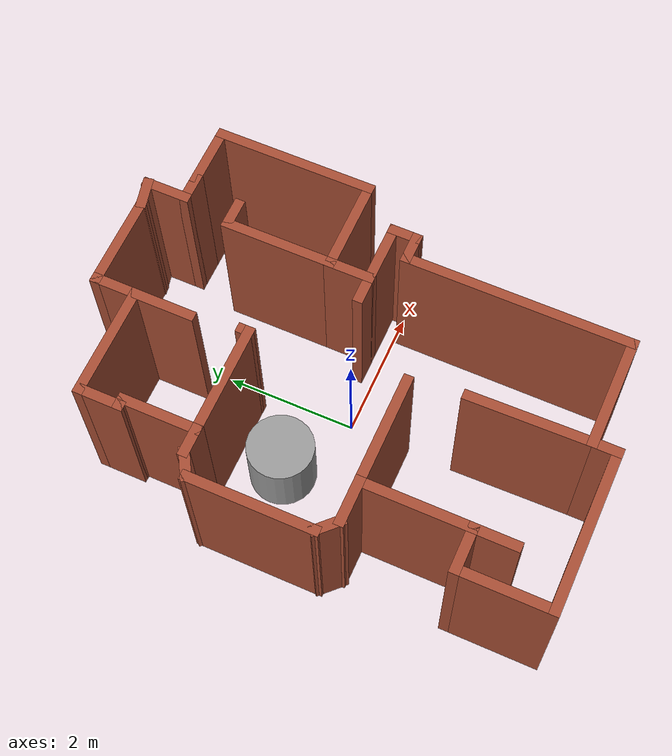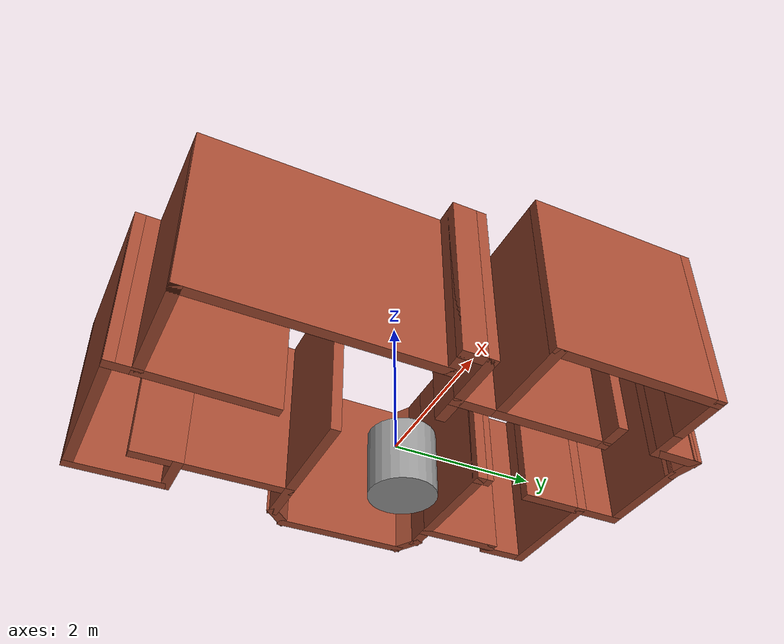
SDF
<?xml version='1.0'?>
<sdf version='1.6'>
  <model name='map_41'>
    <link name='Wall_1'>
      <pose frame=''>0.319898 3.71517 0 0 -0 3.14159</pose>
      <self_collide>0</self_collide>
      <enable_wind>0</enable_wind>
      <kinematic>0</kinematic>
      <visual name='Wall_1_Visual'>
        <pose frame=''>0 0 1.25 0 -0 0</pose>
        <geometry>
          <box>
            <size>1.5 0.15 2.5</size>
          </box>
        </geometry>
        <material>
          <script>
            <uri>file://media/materials/scripts/gazebo.material</uri>
            <name>Gazebo/Bricks</name>
          </script>
          <ambient>1 1 1 1</ambient>
          <shader type='pixel'/>
        </material>
        <meta>
          <layer>0</layer>
        </meta>
        <transparency>0</transparency>
        <cast_shadows>1</cast_shadows>
      </visual>
      <collision name='Wall_1_Collision'>
        <laser_retro>0</laser_retro>
        <max_contacts>10</max_contacts>
        <pose frame=''>0 0 1.25 0 -0 0</pose>
        <geometry>
          <box>
            <size>1.5 0.15 2.5</size>
          </box>
        </geometry>
        <surface>
          <friction>
            <ode>
              <mu>1</mu>
              <mu2>1</mu2>
              <fdir1>0 0 0</fdir1>
              <slip1>0</slip1>
              <slip2>0</slip2>
            </ode>
            <torsional>
              <coefficient>1</coefficient>
              <patch_radius>0</patch_radius>
              <surface_radius>0</surface_radius>
              <use_patch_radius>1</use_patch_radius>
              <ode>
                <slip>0</slip>
              </ode>
            </torsional>
          </friction>
          <bounce>
            <restitution_coefficient>0</restitution_coefficient>
            <threshold>1e+06</threshold>
          </bounce>
          <contact>
            <collide_without_contact>0</collide_without_contact>
            <collide_without_contact_bitmask>1</collide_without_contact_bitmask>
            <collide_bitmask>1</collide_bitmask>
            <ode>
              <soft_cfm>0</soft_cfm>
              <soft_erp>0.2</soft_erp>
              <kp>1e+13</kp>
              <kd>1</kd>
              <max_vel>0.01</max_vel>
              <min_depth>0</min_depth>
            </ode>
            <bullet>
              <split_impulse>1</split_impulse>
              <split_impulse_penetration_threshold>-0.01</split_impulse_penetration_threshold>
              <soft_cfm>0</soft_cfm>
              <soft_erp>0.2</soft_erp>
              <kp>1e+13</kp>
              <kd>1</kd>
            </bullet>
          </contact>
        </surface>
      </collision>
    </link>
    <link name='Wall_10'>
      <pose frame=''>-2.38447 -0.733575 0 0 0 -0.785398</pose>
      <self_collide>0</self_collide>
      <enable_wind>0</enable_wind>
      <kinematic>0</kinematic>
      <visual name='Wall_10_Visual'>
        <pose frame=''>0 0 1.25 0 -0 0</pose>
        <geometry>
          <box>
            <size>0.5 0.15 2.5</size>
          </box>
        </geometry>
        <material>
          <script>
            <uri>file://media/materials/scripts/gazebo.material</uri>
            <name>Gazebo/Bricks</name>
          </script>
          <ambient>1 1 1 1</ambient>
          <shader type='pixel'/>
        </material>
        <meta>
          <layer>0</layer>
        </meta>
        <transparency>0</transparency>
        <cast_shadows>1</cast_shadows>
      </visual>
      <collision name='Wall_10_Collision'>
        <laser_retro>0</laser_retro>
        <max_contacts>10</max_contacts>
        <pose frame=''>0 0 1.25 0 -0 0</pose>
        <geometry>
          <box>
            <size>0.5 0.15 2.5</size>
          </box>
        </geometry>
        <surface>
          <friction>
            <ode>
              <mu>1</mu>
              <mu2>1</mu2>
              <fdir1>0 0 0</fdir1>
              <slip1>0</slip1>
              <slip2>0</slip2>
            </ode>
            <torsional>
              <coefficient>1</coefficient>
              <patch_radius>0</patch_radius>
              <surface_radius>0</surface_radius>
              <use_patch_radius>1</use_patch_radius>
              <ode>
                <slip>0</slip>
              </ode>
            </torsional>
          </friction>
          <bounce>
            <restitution_coefficient>0</restitution_coefficient>
            <threshold>1e+06</threshold>
          </bounce>
          <contact>
            <collide_without_contact>0</collide_without_contact>
            <collide_without_contact_bitmask>1</collide_without_contact_bitmask>
            <collide_bitmask>1</collide_bitmask>
            <ode>
              <soft_cfm>0</soft_cfm>
              <soft_erp>0.2</soft_erp>
              <kp>1e+13</kp>
              <kd>1</kd>
              <max_vel>0.01</max_vel>
              <min_depth>0</min_depth>
            </ode>
            <bullet>
              <split_impulse>1</split_impulse>
              <split_impulse_penetration_threshold>-0.01</split_impulse_penetration_threshold>
              <soft_cfm>0</soft_cfm>
              <soft_erp>0.2</soft_erp>
              <kp>1e+13</kp>
              <kd>1</kd>
            </bullet>
          </contact>
        </surface>
      </collision>
    </link>
    <link name='Wall_11'>
      <pose frame=''>-1.96072 -0.857319 0 0 -0 0</pose>
      <self_collide>0</self_collide>
      <enable_wind>0</enable_wind>
      <kinematic>0</kinematic>
      <visual name='Wall_11_Visual'>
        <pose frame=''>0 0 1.25 0 -0 0</pose>
        <geometry>
          <box>
            <size>0.75 0.15 2.5</size>
          </box>
        </geometry>
        <material>
          <script>
            <uri>file://media/materials/scripts/gazebo.material</uri>
            <name>Gazebo/Bricks</name>
          </script>
          <ambient>1 1 1 1</ambient>
          <shader type='pixel'/>
        </material>
        <meta>
          <layer>0</layer>
        </meta>
        <transparency>0</transparency>
        <cast_shadows>1</cast_shadows>
      </visual>
      <collision name='Wall_11_Collision'>
        <laser_retro>0</laser_retro>
        <max_contacts>10</max_contacts>
        <pose frame=''>0 0 1.25 0 -0 0</pose>
        <geometry>
          <box>
            <size>0.75 0.15 2.5</size>
          </box>
        </geometry>
        <surface>
          <friction>
            <ode>
              <mu>1</mu>
              <mu2>1</mu2>
              <fdir1>0 0 0</fdir1>
              <slip1>0</slip1>
              <slip2>0</slip2>
            </ode>
            <torsional>
              <coefficient>1</coefficient>
              <patch_radius>0</patch_radius>
              <surface_radius>0</surface_radius>
              <use_patch_radius>1</use_patch_radius>
              <ode>
                <slip>0</slip>
              </ode>
            </torsional>
          </friction>
          <bounce>
            <restitution_coefficient>0</restitution_coefficient>
            <threshold>1e+06</threshold>
          </bounce>
          <contact>
            <collide_without_contact>0</collide_without_contact>
            <collide_without_contact_bitmask>1</collide_without_contact_bitmask>
            <collide_bitmask>1</collide_bitmask>
            <ode>
              <soft_cfm>0</soft_cfm>
              <soft_erp>0.2</soft_erp>
              <kp>1e+13</kp>
              <kd>1</kd>
              <max_vel>0.01</max_vel>
              <min_depth>0</min_depth>
            </ode>
            <bullet>
              <split_impulse>1</split_impulse>
              <split_impulse_penetration_threshold>-0.01</split_impulse_penetration_threshold>
              <soft_cfm>0</soft_cfm>
              <soft_erp>0.2</soft_erp>
              <kp>1e+13</kp>
              <kd>1</kd>
            </bullet>
          </contact>
        </surface>
      </collision>
    </link>
    <link name='Wall_12'>
      <pose frame=''>-1.66072 -1.65732 0 0 0 -1.5708</pose>
      <self_collide>0</self_collide>
      <enable_wind>0</enable_wind>
      <kinematic>0</kinematic>
      <visual name='Wall_12_Visual'>
        <pose frame=''>0 0 1.25 0 -0 0</pose>
        <geometry>
          <box>
            <size>1.75 0.15 2.5</size>
          </box>
        </geometry>
        <material>
          <script>
            <uri>file://media/materials/scripts/gazebo.material</uri>
            <name>Gazebo/Bricks</name>
          </script>
          <ambient>1 1 1 1</ambient>
          <shader type='pixel'/>
        </material>
        <meta>
          <layer>0</layer>
        </meta>
        <transparency>0</transparency>
        <cast_shadows>1</cast_shadows>
      </visual>
      <collision name='Wall_12_Collision'>
        <laser_retro>0</laser_retro>
        <max_contacts>10</max_contacts>
        <pose frame=''>0 0 1.25 0 -0 0</pose>
        <geometry>
          <box>
            <size>1.75 0.15 2.5</size>
          </box>
        </geometry>
        <surface>
          <friction>
            <ode>
              <mu>1</mu>
              <mu2>1</mu2>
              <fdir1>0 0 0</fdir1>
              <slip1>0</slip1>
              <slip2>0</slip2>
            </ode>
            <torsional>
              <coefficient>1</coefficient>
              <patch_radius>0</patch_radius>
              <surface_radius>0</surface_radius>
              <use_patch_radius>1</use_patch_radius>
              <ode>
                <slip>0</slip>
              </ode>
            </torsional>
          </friction>
          <bounce>
            <restitution_coefficient>0</restitution_coefficient>
            <threshold>1e+06</threshold>
          </bounce>
          <contact>
            <collide_without_contact>0</collide_without_contact>
            <collide_without_contact_bitmask>1</collide_without_contact_bitmask>
            <collide_bitmask>1</collide_bitmask>
            <ode>
              <soft_cfm>0</soft_cfm>
              <soft_erp>0.2</soft_erp>
              <kp>1e+13</kp>
              <kd>1</kd>
              <max_vel>0.01</max_vel>
              <min_depth>0</min_depth>
            </ode>
            <bullet>
              <split_impulse>1</split_impulse>
              <split_impulse_penetration_threshold>-0.01</split_impulse_penetration_threshold>
              <soft_cfm>0</soft_cfm>
              <soft_erp>0.2</soft_erp>
              <kp>1e+13</kp>
              <kd>1</kd>
            </bullet>
          </contact>
        </surface>
      </collision>
    </link>
    <link name='Wall_13'>
      <pose frame=''>-1.96072 -2.45732 0 0 -0 3.14159</pose>
      <self_collide>0</self_collide>
      <enable_wind>0</enable_wind>
      <kinematic>0</kinematic>
      <visual name='Wall_13_Visual'>
        <pose frame=''>0 0 1.25 0 -0 0</pose>
        <geometry>
          <box>
            <size>0.75 0.15 2.5</size>
          </box>
        </geometry>
        <material>
          <script>
            <uri>file://media/materials/scripts/gazebo.material</uri>
            <name>Gazebo/Bricks</name>
          </script>
          <ambient>1 1 1 1</ambient>
          <shader type='pixel'/>
        </material>
        <meta>
          <layer>0</layer>
        </meta>
        <transparency>0</transparency>
        <cast_shadows>1</cast_shadows>
      </visual>
      <collision name='Wall_13_Collision'>
        <laser_retro>0</laser_retro>
        <max_contacts>10</max_contacts>
        <pose frame=''>0 0 1.25 0 -0 0</pose>
        <geometry>
          <box>
            <size>0.75 0.15 2.5</size>
          </box>
        </geometry>
        <surface>
          <friction>
            <ode>
              <mu>1</mu>
              <mu2>1</mu2>
              <fdir1>0 0 0</fdir1>
              <slip1>0</slip1>
              <slip2>0</slip2>
            </ode>
            <torsional>
              <coefficient>1</coefficient>
              <patch_radius>0</patch_radius>
              <surface_radius>0</surface_radius>
              <use_patch_radius>1</use_patch_radius>
              <ode>
                <slip>0</slip>
              </ode>
            </torsional>
          </friction>
          <bounce>
            <restitution_coefficient>0</restitution_coefficient>
            <threshold>1e+06</threshold>
          </bounce>
          <contact>
            <collide_without_contact>0</collide_without_contact>
            <collide_without_contact_bitmask>1</collide_without_contact_bitmask>
            <collide_bitmask>1</collide_bitmask>
            <ode>
              <soft_cfm>0</soft_cfm>
              <soft_erp>0.2</soft_erp>
              <kp>1e+13</kp>
              <kd>1</kd>
              <max_vel>0.01</max_vel>
              <min_depth>0</min_depth>
            </ode>
            <bullet>
              <split_impulse>1</split_impulse>
              <split_impulse_penetration_threshold>-0.01</split_impulse_penetration_threshold>
              <soft_cfm>0</soft_cfm>
              <soft_erp>0.2</soft_erp>
              <kp>1e+13</kp>
              <kd>1</kd>
            </bullet>
          </contact>
        </surface>
      </collision>
    </link>
    <link name='Wall_14'>
      <pose frame=''>-2.26072 -3.13232 0 0 0 -1.5708</pose>
      <self_collide>0</self_collide>
      <enable_wind>0</enable_wind>
      <kinematic>0</kinematic>
      <visual name='Wall_14_Visual'>
        <pose frame=''>0 0 1.25 0 -0 0</pose>
        <geometry>
          <box>
            <size>1.5 0.15 2.5</size>
          </box>
        </geometry>
        <material>
          <script>
            <uri>file://media/materials/scripts/gazebo.material</uri>
            <name>Gazebo/Bricks</name>
          </script>
          <ambient>1 1 1 1</ambient>
          <shader type='pixel'/>
        </material>
        <meta>
          <layer>0</layer>
        </meta>
        <transparency>0</transparency>
        <cast_shadows>1</cast_shadows>
      </visual>
      <collision name='Wall_14_Collision'>
        <laser_retro>0</laser_retro>
        <max_contacts>10</max_contacts>
        <pose frame=''>0 0 1.25 0 -0 0</pose>
        <geometry>
          <box>
            <size>1.5 0.15 2.5</size>
          </box>
        </geometry>
        <surface>
          <friction>
            <ode>
              <mu>1</mu>
              <mu2>1</mu2>
              <fdir1>0 0 0</fdir1>
              <slip1>0</slip1>
              <slip2>0</slip2>
            </ode>
            <torsional>
              <coefficient>1</coefficient>
              <patch_radius>0</patch_radius>
              <surface_radius>0</surface_radius>
              <use_patch_radius>1</use_patch_radius>
              <ode>
                <slip>0</slip>
              </ode>
            </torsional>
          </friction>
          <bounce>
            <restitution_coefficient>0</restitution_coefficient>
            <threshold>1e+06</threshold>
          </bounce>
          <contact>
            <collide_without_contact>0</collide_without_contact>
            <collide_without_contact_bitmask>1</collide_without_contact_bitmask>
            <collide_bitmask>1</collide_bitmask>
            <ode>
              <soft_cfm>0</soft_cfm>
              <soft_erp>0.2</soft_erp>
              <kp>1e+13</kp>
              <kd>1</kd>
              <max_vel>0.01</max_vel>
              <min_depth>0</min_depth>
            </ode>
            <bullet>
              <split_impulse>1</split_impulse>
              <split_impulse_penetration_threshold>-0.01</split_impulse_penetration_threshold>
              <soft_cfm>0</soft_cfm>
              <soft_erp>0.2</soft_erp>
              <kp>1e+13</kp>
              <kd>1</kd>
            </bullet>
          </contact>
        </surface>
      </collision>
    </link>
    <link name='Wall_15'>
      <pose frame=''>-1.08572 -3.80732 0 0 -0 0</pose>
      <self_collide>0</self_collide>
      <enable_wind>0</enable_wind>
      <kinematic>0</kinematic>
      <visual name='Wall_15_Visual'>
        <pose frame=''>0 0 1.25 0 -0 0</pose>
        <geometry>
          <box>
            <size>2.5 0.15 2.5</size>
          </box>
        </geometry>
        <material>
          <script>
            <uri>file://media/materials/scripts/gazebo.material</uri>
            <name>Gazebo/Bricks</name>
          </script>
          <ambient>1 1 1 1</ambient>
          <shader type='pixel'/>
        </material>
        <meta>
          <layer>0</layer>
        </meta>
        <transparency>0</transparency>
        <cast_shadows>1</cast_shadows>
      </visual>
      <collision name='Wall_15_Collision'>
        <laser_retro>0</laser_retro>
        <max_contacts>10</max_contacts>
        <pose frame=''>0 0 1.25 0 -0 0</pose>
        <geometry>
          <box>
            <size>2.5 0.15 2.5</size>
          </box>
        </geometry>
        <surface>
          <friction>
            <ode>
              <mu>1</mu>
              <mu2>1</mu2>
              <fdir1>0 0 0</fdir1>
              <slip1>0</slip1>
              <slip2>0</slip2>
            </ode>
            <torsional>
              <coefficient>1</coefficient>
              <patch_radius>0</patch_radius>
              <surface_radius>0</surface_radius>
              <use_patch_radius>1</use_patch_radius>
              <ode>
                <slip>0</slip>
              </ode>
            </torsional>
          </friction>
          <bounce>
            <restitution_coefficient>0</restitution_coefficient>
            <threshold>1e+06</threshold>
          </bounce>
          <contact>
            <collide_without_contact>0</collide_without_contact>
            <collide_without_contact_bitmask>1</collide_without_contact_bitmask>
            <collide_bitmask>1</collide_bitmask>
            <ode>
              <soft_cfm>0</soft_cfm>
              <soft_erp>0.2</soft_erp>
              <kp>1e+13</kp>
              <kd>1</kd>
              <max_vel>0.01</max_vel>
              <min_depth>0</min_depth>
            </ode>
            <bullet>
              <split_impulse>1</split_impulse>
              <split_impulse_penetration_threshold>-0.01</split_impulse_penetration_threshold>
              <soft_cfm>0</soft_cfm>
              <soft_erp>0.2</soft_erp>
              <kp>1e+13</kp>
              <kd>1</kd>
            </bullet>
          </contact>
        </surface>
      </collision>
    </link>
    <link name='Wall_16'>
      <pose frame=''>0.089277 -3.63232 0 0 -0 1.5708</pose>
      <self_collide>0</self_collide>
      <enable_wind>0</enable_wind>
      <kinematic>0</kinematic>
      <visual name='Wall_16_Visual'>
        <pose frame=''>0 0 1.25 0 -0 0</pose>
        <geometry>
          <box>
            <size>0.5 0.15 2.5</size>
          </box>
        </geometry>
        <material>
          <script>
            <uri>file://media/materials/scripts/gazebo.material</uri>
            <name>Gazebo/Bricks</name>
          </script>
          <ambient>1 1 1 1</ambient>
          <shader type='pixel'/>
        </material>
        <meta>
          <layer>0</layer>
        </meta>
        <transparency>0</transparency>
        <cast_shadows>1</cast_shadows>
      </visual>
      <collision name='Wall_16_Collision'>
        <laser_retro>0</laser_retro>
        <max_contacts>10</max_contacts>
        <pose frame=''>0 0 1.25 0 -0 0</pose>
        <geometry>
          <box>
            <size>0.5 0.15 2.5</size>
          </box>
        </geometry>
        <surface>
          <friction>
            <ode>
              <mu>1</mu>
              <mu2>1</mu2>
              <fdir1>0 0 0</fdir1>
              <slip1>0</slip1>
              <slip2>0</slip2>
            </ode>
            <torsional>
              <coefficient>1</coefficient>
              <patch_radius>0</patch_radius>
              <surface_radius>0</surface_radius>
              <use_patch_radius>1</use_patch_radius>
              <ode>
                <slip>0</slip>
              </ode>
            </torsional>
          </friction>
          <bounce>
            <restitution_coefficient>0</restitution_coefficient>
            <threshold>1e+06</threshold>
          </bounce>
          <contact>
            <collide_without_contact>0</collide_without_contact>
            <collide_without_contact_bitmask>1</collide_without_contact_bitmask>
            <collide_bitmask>1</collide_bitmask>
            <ode>
              <soft_cfm>0</soft_cfm>
              <soft_erp>0.2</soft_erp>
              <kp>1e+13</kp>
              <kd>1</kd>
              <max_vel>0.01</max_vel>
              <min_depth>0</min_depth>
            </ode>
            <bullet>
              <split_impulse>1</split_impulse>
              <split_impulse_penetration_threshold>-0.01</split_impulse_penetration_threshold>
              <soft_cfm>0</soft_cfm>
              <soft_erp>0.2</soft_erp>
              <kp>1e+13</kp>
              <kd>1</kd>
            </bullet>
          </contact>
        </surface>
      </collision>
    </link>
    <link name='Wall_19'>
      <pose frame=''>0.889277 -3.45732 0 0 -0 0</pose>
      <self_collide>0</self_collide>
      <enable_wind>0</enable_wind>
      <kinematic>0</kinematic>
      <visual name='Wall_19_Visual'>
        <pose frame=''>0 0 1.25 0 -0 0</pose>
        <geometry>
          <box>
            <size>1.75 0.15 2.5</size>
          </box>
        </geometry>
        <material>
          <script>
            <uri>file://media/materials/scripts/gazebo.material</uri>
            <name>Gazebo/Bricks</name>
          </script>
          <ambient>1 1 1 1</ambient>
          <shader type='pixel'/>
        </material>
        <meta>
          <layer>0</layer>
        </meta>
        <transparency>0</transparency>
        <cast_shadows>1</cast_shadows>
      </visual>
      <collision name='Wall_19_Collision'>
        <laser_retro>0</laser_retro>
        <max_contacts>10</max_contacts>
        <pose frame=''>0 0 1.25 0 -0 0</pose>
        <geometry>
          <box>
            <size>1.75 0.15 2.5</size>
          </box>
        </geometry>
        <surface>
          <friction>
            <ode>
              <mu>1</mu>
              <mu2>1</mu2>
              <fdir1>0 0 0</fdir1>
              <slip1>0</slip1>
              <slip2>0</slip2>
            </ode>
            <torsional>
              <coefficient>1</coefficient>
              <patch_radius>0</patch_radius>
              <surface_radius>0</surface_radius>
              <use_patch_radius>1</use_patch_radius>
              <ode>
                <slip>0</slip>
              </ode>
            </torsional>
          </friction>
          <bounce>
            <restitution_coefficient>0</restitution_coefficient>
            <threshold>1e+06</threshold>
          </bounce>
          <contact>
            <collide_without_contact>0</collide_without_contact>
            <collide_without_contact_bitmask>1</collide_without_contact_bitmask>
            <collide_bitmask>1</collide_bitmask>
            <ode>
              <soft_cfm>0</soft_cfm>
              <soft_erp>0.2</soft_erp>
              <kp>1e+13</kp>
              <kd>1</kd>
              <max_vel>0.01</max_vel>
              <min_depth>0</min_depth>
            </ode>
            <bullet>
              <split_impulse>1</split_impulse>
              <split_impulse_penetration_threshold>-0.01</split_impulse_penetration_threshold>
              <soft_cfm>0</soft_cfm>
              <soft_erp>0.2</soft_erp>
              <kp>1e+13</kp>
              <kd>1</kd>
            </bullet>
          </contact>
        </surface>
      </collision>
    </link>
    <link name='Wall_2'>
      <pose frame=''>-0.355102 3.41517 0 0 0 -1.5708</pose>
      <self_collide>0</self_collide>
      <enable_wind>0</enable_wind>
      <kinematic>0</kinematic>
      <visual name='Wall_2_Visual'>
        <pose frame=''>0 0 1.25 0 -0 0</pose>
        <geometry>
          <box>
            <size>0.75 0.15 2.5</size>
          </box>
        </geometry>
        <material>
          <script>
            <uri>file://media/materials/scripts/gazebo.material</uri>
            <name>Gazebo/Bricks</name>
          </script>
          <ambient>1 1 1 1</ambient>
          <shader type='pixel'/>
        </material>
        <meta>
          <layer>0</layer>
        </meta>
        <transparency>0</transparency>
        <cast_shadows>1</cast_shadows>
      </visual>
      <collision name='Wall_2_Collision'>
        <laser_retro>0</laser_retro>
        <max_contacts>10</max_contacts>
        <pose frame=''>0 0 1.25 0 -0 0</pose>
        <geometry>
          <box>
            <size>0.75 0.15 2.5</size>
          </box>
        </geometry>
        <surface>
          <friction>
            <ode>
              <mu>1</mu>
              <mu2>1</mu2>
              <fdir1>0 0 0</fdir1>
              <slip1>0</slip1>
              <slip2>0</slip2>
            </ode>
            <torsional>
              <coefficient>1</coefficient>
              <patch_radius>0</patch_radius>
              <surface_radius>0</surface_radius>
              <use_patch_radius>1</use_patch_radius>
              <ode>
                <slip>0</slip>
              </ode>
            </torsional>
          </friction>
          <bounce>
            <restitution_coefficient>0</restitution_coefficient>
            <threshold>1e+06</threshold>
          </bounce>
          <contact>
            <collide_without_contact>0</collide_without_contact>
            <collide_without_contact_bitmask>1</collide_without_contact_bitmask>
            <collide_bitmask>1</collide_bitmask>
            <ode>
              <soft_cfm>0</soft_cfm>
              <soft_erp>0.2</soft_erp>
              <kp>1e+13</kp>
              <kd>1</kd>
              <max_vel>0.01</max_vel>
              <min_depth>0</min_depth>
            </ode>
            <bullet>
              <split_impulse>1</split_impulse>
              <split_impulse_penetration_threshold>-0.01</split_impulse_penetration_threshold>
              <soft_cfm>0</soft_cfm>
              <soft_erp>0.2</soft_erp>
              <kp>1e+13</kp>
              <kd>1</kd>
            </bullet>
          </contact>
        </surface>
      </collision>
    </link>
    <link name='Wall_20'>
      <pose frame=''>1.68928 -1.78232 0 0 -0 1.5708</pose>
      <self_collide>0</self_collide>
      <enable_wind>0</enable_wind>
      <kinematic>0</kinematic>
      <visual name='Wall_20_Visual'>
        <pose frame=''>0 0 1.25 0 -0 0</pose>
        <geometry>
          <box>
            <size>3.5 0.15 2.5</size>
          </box>
        </geometry>
        <material>
          <script>
            <uri>file://media/materials/scripts/gazebo.material</uri>
            <name>Gazebo/Bricks</name>
          </script>
          <ambient>1 1 1 1</ambient>
          <shader type='pixel'/>
        </material>
        <meta>
          <layer>0</layer>
        </meta>
        <transparency>0</transparency>
        <cast_shadows>1</cast_shadows>
      </visual>
      <collision name='Wall_20_Collision'>
        <laser_retro>0</laser_retro>
        <max_contacts>10</max_contacts>
        <pose frame=''>0 0 1.25 0 -0 0</pose>
        <geometry>
          <box>
            <size>3.5 0.15 2.5</size>
          </box>
        </geometry>
        <surface>
          <friction>
            <ode>
              <mu>1</mu>
              <mu2>1</mu2>
              <fdir1>0 0 0</fdir1>
              <slip1>0</slip1>
              <slip2>0</slip2>
            </ode>
            <torsional>
              <coefficient>1</coefficient>
              <patch_radius>0</patch_radius>
              <surface_radius>0</surface_radius>
              <use_patch_radius>1</use_patch_radius>
              <ode>
                <slip>0</slip>
              </ode>
            </torsional>
          </friction>
          <bounce>
            <restitution_coefficient>0</restitution_coefficient>
            <threshold>1e+06</threshold>
          </bounce>
          <contact>
            <collide_without_contact>0</collide_without_contact>
            <collide_without_contact_bitmask>1</collide_without_contact_bitmask>
            <collide_bitmask>1</collide_bitmask>
            <ode>
              <soft_cfm>0</soft_cfm>
              <soft_erp>0.2</soft_erp>
              <kp>1e+13</kp>
              <kd>1</kd>
              <max_vel>0.01</max_vel>
              <min_depth>0</min_depth>
            </ode>
            <bullet>
              <split_impulse>1</split_impulse>
              <split_impulse_penetration_threshold>-0.01</split_impulse_penetration_threshold>
              <soft_cfm>0</soft_cfm>
              <soft_erp>0.2</soft_erp>
              <kp>1e+13</kp>
              <kd>1</kd>
            </bullet>
          </contact>
        </surface>
      </collision>
    </link>
    <link name='Wall_21'>
      <pose frame=''>1.86428 -0.107319 0 0 -0 0</pose>
      <self_collide>0</self_collide>
      <enable_wind>0</enable_wind>
      <kinematic>0</kinematic>
      <visual name='Wall_21_Visual'>
        <pose frame=''>0 0 1.25 0 -0 0</pose>
        <geometry>
          <box>
            <size>0.5 0.15 2.5</size>
          </box>
        </geometry>
        <material>
          <script>
            <uri>file://media/materials/scripts/gazebo.material</uri>
            <name>Gazebo/Bricks</name>
          </script>
          <ambient>1 1 1 1</ambient>
          <shader type='pixel'/>
        </material>
        <meta>
          <layer>0</layer>
        </meta>
        <transparency>0</transparency>
        <cast_shadows>1</cast_shadows>
      </visual>
      <collision name='Wall_21_Collision'>
        <laser_retro>0</laser_retro>
        <max_contacts>10</max_contacts>
        <pose frame=''>0 0 1.25 0 -0 0</pose>
        <geometry>
          <box>
            <size>0.5 0.15 2.5</size>
          </box>
        </geometry>
        <surface>
          <friction>
            <ode>
              <mu>1</mu>
              <mu2>1</mu2>
              <fdir1>0 0 0</fdir1>
              <slip1>0</slip1>
              <slip2>0</slip2>
            </ode>
            <torsional>
              <coefficient>1</coefficient>
              <patch_radius>0</patch_radius>
              <surface_radius>0</surface_radius>
              <use_patch_radius>1</use_patch_radius>
              <ode>
                <slip>0</slip>
              </ode>
            </torsional>
          </friction>
          <bounce>
            <restitution_coefficient>0</restitution_coefficient>
            <threshold>1e+06</threshold>
          </bounce>
          <contact>
            <collide_without_contact>0</collide_without_contact>
            <collide_without_contact_bitmask>1</collide_without_contact_bitmask>
            <collide_bitmask>1</collide_bitmask>
            <ode>
              <soft_cfm>0</soft_cfm>
              <soft_erp>0.2</soft_erp>
              <kp>1e+13</kp>
              <kd>1</kd>
              <max_vel>0.01</max_vel>
              <min_depth>0</min_depth>
            </ode>
            <bullet>
              <split_impulse>1</split_impulse>
              <split_impulse_penetration_threshold>-0.01</split_impulse_penetration_threshold>
              <soft_cfm>0</soft_cfm>
              <soft_erp>0.2</soft_erp>
              <kp>1e+13</kp>
              <kd>1</kd>
            </bullet>
          </contact>
        </surface>
      </collision>
    </link>
    <link name='Wall_22'>
      <pose frame=''>2.03928 0.067681 0 0 -0 1.5708</pose>
      <self_collide>0</self_collide>
      <enable_wind>0</enable_wind>
      <kinematic>0</kinematic>
      <visual name='Wall_22_Visual'>
        <pose frame=''>0 0 1.25 0 -0 0</pose>
        <geometry>
          <box>
            <size>0.5 0.15 2.5</size>
          </box>
        </geometry>
        <material>
          <script>
            <uri>file://media/materials/scripts/gazebo.material</uri>
            <name>Gazebo/Bricks</name>
          </script>
          <ambient>1 1 1 1</ambient>
          <shader type='pixel'/>
        </material>
        <meta>
          <layer>0</layer>
        </meta>
        <transparency>0</transparency>
        <cast_shadows>1</cast_shadows>
      </visual>
      <collision name='Wall_22_Collision'>
        <laser_retro>0</laser_retro>
        <max_contacts>10</max_contacts>
        <pose frame=''>0 0 1.25 0 -0 0</pose>
        <geometry>
          <box>
            <size>0.5 0.15 2.5</size>
          </box>
        </geometry>
        <surface>
          <friction>
            <ode>
              <mu>1</mu>
              <mu2>1</mu2>
              <fdir1>0 0 0</fdir1>
              <slip1>0</slip1>
              <slip2>0</slip2>
            </ode>
            <torsional>
              <coefficient>1</coefficient>
              <patch_radius>0</patch_radius>
              <surface_radius>0</surface_radius>
              <use_patch_radius>1</use_patch_radius>
              <ode>
                <slip>0</slip>
              </ode>
            </torsional>
          </friction>
          <bounce>
            <restitution_coefficient>0</restitution_coefficient>
            <threshold>1e+06</threshold>
          </bounce>
          <contact>
            <collide_without_contact>0</collide_without_contact>
            <collide_without_contact_bitmask>1</collide_without_contact_bitmask>
            <collide_bitmask>1</collide_bitmask>
            <ode>
              <soft_cfm>0</soft_cfm>
              <soft_erp>0.2</soft_erp>
              <kp>1e+13</kp>
              <kd>1</kd>
              <max_vel>0.01</max_vel>
              <min_depth>0</min_depth>
            </ode>
            <bullet>
              <split_impulse>1</split_impulse>
              <split_impulse_penetration_threshold>-0.01</split_impulse_penetration_threshold>
              <soft_cfm>0</soft_cfm>
              <soft_erp>0.2</soft_erp>
              <kp>1e+13</kp>
              <kd>1</kd>
            </bullet>
          </contact>
        </surface>
      </collision>
    </link>
    <link name='Wall_24'>
      <pose frame=''>-0.860723 -0.857319 0 0 -0 0</pose>
      <self_collide>0</self_collide>
      <enable_wind>0</enable_wind>
      <kinematic>0</kinematic>
      <visual name='Wall_24_Visual'>
        <pose frame=''>0 0 1.25 0 -0 0</pose>
        <geometry>
          <box>
            <size>1.75 0.15 2.5</size>
          </box>
        </geometry>
        <material>
          <script>
            <uri>file://media/materials/scripts/gazebo.material</uri>
            <name>Gazebo/Bricks</name>
          </script>
          <ambient>1 1 1 1</ambient>
          <shader type='pixel'/>
        </material>
        <meta>
          <layer>0</layer>
        </meta>
        <transparency>0</transparency>
        <cast_shadows>1</cast_shadows>
      </visual>
      <collision name='Wall_24_Collision'>
        <laser_retro>0</laser_retro>
        <max_contacts>10</max_contacts>
        <pose frame=''>0 0 1.25 0 -0 0</pose>
        <geometry>
          <box>
            <size>1.75 0.15 2.5</size>
          </box>
        </geometry>
        <surface>
          <friction>
            <ode>
              <mu>1</mu>
              <mu2>1</mu2>
              <fdir1>0 0 0</fdir1>
              <slip1>0</slip1>
              <slip2>0</slip2>
            </ode>
            <torsional>
              <coefficient>1</coefficient>
              <patch_radius>0</patch_radius>
              <surface_radius>0</surface_radius>
              <use_patch_radius>1</use_patch_radius>
              <ode>
                <slip>0</slip>
              </ode>
            </torsional>
          </friction>
          <bounce>
            <restitution_coefficient>0</restitution_coefficient>
            <threshold>1e+06</threshold>
          </bounce>
          <contact>
            <collide_without_contact>0</collide_without_contact>
            <collide_without_contact_bitmask>1</collide_without_contact_bitmask>
            <collide_bitmask>1</collide_bitmask>
            <ode>
              <soft_cfm>0</soft_cfm>
              <soft_erp>0.2</soft_erp>
              <kp>1e+13</kp>
              <kd>1</kd>
              <max_vel>0.01</max_vel>
              <min_depth>0</min_depth>
            </ode>
            <bullet>
              <split_impulse>1</split_impulse>
              <split_impulse_penetration_threshold>-0.01</split_impulse_penetration_threshold>
              <soft_cfm>0</soft_cfm>
              <soft_erp>0.2</soft_erp>
              <kp>1e+13</kp>
              <kd>1</kd>
            </bullet>
          </contact>
        </surface>
      </collision>
    </link>
    <link name='Wall_26'>
      <pose frame=''>0.0726 -2.57559 0 0 0 -1.55188</pose>
      <self_collide>0</self_collide>
      <enable_wind>0</enable_wind>
      <kinematic>0</kinematic>
      <visual name='Wall_26_Visual'>
        <pose frame=''>0 0 1.25 0 -0 0</pose>
        <geometry>
          <box>
            <size>1.91378 0.15 2.5</size>
          </box>
        </geometry>
        <material>
          <script>
            <uri>file://media/materials/scripts/gazebo.material</uri>
            <name>Gazebo/Bricks</name>
          </script>
          <ambient>1 1 1 1</ambient>
          <shader type='pixel'/>
        </material>
        <meta>
          <layer>0</layer>
        </meta>
        <transparency>0</transparency>
        <cast_shadows>1</cast_shadows>
      </visual>
      <collision name='Wall_26_Collision'>
        <laser_retro>0</laser_retro>
        <max_contacts>10</max_contacts>
        <pose frame=''>0 0 1.25 0 -0 0</pose>
        <geometry>
          <box>
            <size>1.91378 0.15 2.5</size>
          </box>
        </geometry>
        <surface>
          <friction>
            <ode>
              <mu>1</mu>
              <mu2>1</mu2>
              <fdir1>0 0 0</fdir1>
              <slip1>0</slip1>
              <slip2>0</slip2>
            </ode>
            <torsional>
              <coefficient>1</coefficient>
              <patch_radius>0</patch_radius>
              <surface_radius>0</surface_radius>
              <use_patch_radius>1</use_patch_radius>
              <ode>
                <slip>0</slip>
              </ode>
            </torsional>
          </friction>
          <bounce>
            <restitution_coefficient>0</restitution_coefficient>
            <threshold>1e+06</threshold>
          </bounce>
          <contact>
            <collide_without_contact>0</collide_without_contact>
            <collide_without_contact_bitmask>1</collide_without_contact_bitmask>
            <collide_bitmask>1</collide_bitmask>
            <ode>
              <soft_cfm>0</soft_cfm>
              <soft_erp>0.2</soft_erp>
              <kp>1e+13</kp>
              <kd>1</kd>
              <max_vel>0.01</max_vel>
              <min_depth>0</min_depth>
            </ode>
            <bullet>
              <split_impulse>1</split_impulse>
              <split_impulse_penetration_threshold>-0.01</split_impulse_penetration_threshold>
              <soft_cfm>0</soft_cfm>
              <soft_erp>0.2</soft_erp>
              <kp>1e+13</kp>
              <kd>1</kd>
            </bullet>
          </contact>
        </surface>
      </collision>
    </link>
    <link name='Wall_3'>
      <pose frame=''>-1.1551 3.11517 0 0 -0 3.14159</pose>
      <self_collide>0</self_collide>
      <enable_wind>0</enable_wind>
      <kinematic>0</kinematic>
      <visual name='Wall_3_Visual'>
        <pose frame=''>0 0 1.25 0 -0 0</pose>
        <geometry>
          <box>
            <size>1.75 0.15 2.5</size>
          </box>
        </geometry>
        <material>
          <script>
            <uri>file://media/materials/scripts/gazebo.material</uri>
            <name>Gazebo/Bricks</name>
          </script>
          <ambient>1 1 1 1</ambient>
          <shader type='pixel'/>
        </material>
        <meta>
          <layer>0</layer>
        </meta>
        <transparency>0</transparency>
        <cast_shadows>1</cast_shadows>
      </visual>
      <collision name='Wall_3_Collision'>
        <laser_retro>0</laser_retro>
        <max_contacts>10</max_contacts>
        <pose frame=''>0 0 1.25 0 -0 0</pose>
        <geometry>
          <box>
            <size>1.75 0.15 2.5</size>
          </box>
        </geometry>
        <surface>
          <friction>
            <ode>
              <mu>1</mu>
              <mu2>1</mu2>
              <fdir1>0 0 0</fdir1>
              <slip1>0</slip1>
              <slip2>0</slip2>
            </ode>
            <torsional>
              <coefficient>1</coefficient>
              <patch_radius>0</patch_radius>
              <surface_radius>0</surface_radius>
              <use_patch_radius>1</use_patch_radius>
              <ode>
                <slip>0</slip>
              </ode>
            </torsional>
          </friction>
          <bounce>
            <restitution_coefficient>0</restitution_coefficient>
            <threshold>1e+06</threshold>
          </bounce>
          <contact>
            <collide_without_contact>0</collide_without_contact>
            <collide_without_contact_bitmask>1</collide_without_contact_bitmask>
            <collide_bitmask>1</collide_bitmask>
            <ode>
              <soft_cfm>0</soft_cfm>
              <soft_erp>0.2</soft_erp>
              <kp>1e+13</kp>
              <kd>1</kd>
              <max_vel>0.01</max_vel>
              <min_depth>0</min_depth>
            </ode>
            <bullet>
              <split_impulse>1</split_impulse>
              <split_impulse_penetration_threshold>-0.01</split_impulse_penetration_threshold>
              <soft_cfm>0</soft_cfm>
              <soft_erp>0.2</soft_erp>
              <kp>1e+13</kp>
              <kd>1</kd>
            </bullet>
          </contact>
        </surface>
      </collision>
    </link>
    <link name='Wall_30'>
      <pose frame=''>-1.66072 -2.75732 0 0 0 -1.5708</pose>
      <self_collide>0</self_collide>
      <enable_wind>0</enable_wind>
      <kinematic>0</kinematic>
      <visual name='Wall_30_Visual'>
        <pose frame=''>0 0 1.25 0 -0 0</pose>
        <geometry>
          <box>
            <size>0.75 0.15 2.5</size>
          </box>
        </geometry>
        <material>
          <script>
            <uri>file://media/materials/scripts/gazebo.material</uri>
            <name>Gazebo/Bricks</name>
          </script>
          <ambient>1 1 1 1</ambient>
          <shader type='pixel'/>
        </material>
        <meta>
          <layer>0</layer>
        </meta>
        <transparency>0</transparency>
        <cast_shadows>1</cast_shadows>
      </visual>
      <collision name='Wall_30_Collision'>
        <laser_retro>0</laser_retro>
        <max_contacts>10</max_contacts>
        <pose frame=''>0 0 1.25 0 -0 0</pose>
        <geometry>
          <box>
            <size>0.75 0.15 2.5</size>
          </box>
        </geometry>
        <surface>
          <friction>
            <ode>
              <mu>1</mu>
              <mu2>1</mu2>
              <fdir1>0 0 0</fdir1>
              <slip1>0</slip1>
              <slip2>0</slip2>
            </ode>
            <torsional>
              <coefficient>1</coefficient>
              <patch_radius>0</patch_radius>
              <surface_radius>0</surface_radius>
              <use_patch_radius>1</use_patch_radius>
              <ode>
                <slip>0</slip>
              </ode>
            </torsional>
          </friction>
          <bounce>
            <restitution_coefficient>0</restitution_coefficient>
            <threshold>1e+06</threshold>
          </bounce>
          <contact>
            <collide_without_contact>0</collide_without_contact>
            <collide_without_contact_bitmask>1</collide_without_contact_bitmask>
            <collide_bitmask>1</collide_bitmask>
            <ode>
              <soft_cfm>0</soft_cfm>
              <soft_erp>0.2</soft_erp>
              <kp>1e+13</kp>
              <kd>1</kd>
              <max_vel>0.01</max_vel>
              <min_depth>0</min_depth>
            </ode>
            <bullet>
              <split_impulse>1</split_impulse>
              <split_impulse_penetration_threshold>-0.01</split_impulse_penetration_threshold>
              <soft_cfm>0</soft_cfm>
              <soft_erp>0.2</soft_erp>
              <kp>1e+13</kp>
              <kd>1</kd>
            </bullet>
          </contact>
        </surface>
      </collision>
    </link>
    <link name='Wall_32'>
      <pose frame=''>1.61428 0.242681 0 0 -0 3.14159</pose>
      <self_collide>0</self_collide>
      <enable_wind>0</enable_wind>
      <kinematic>0</kinematic>
      <visual name='Wall_32_Visual'>
        <pose frame=''>0 0 1.25 0 -0 0</pose>
        <geometry>
          <box>
            <size>1 0.15 2.5</size>
          </box>
        </geometry>
        <material>
          <script>
            <uri>file://media/materials/scripts/gazebo.material</uri>
            <name>Gazebo/Bricks</name>
          </script>
          <ambient>1 1 1 1</ambient>
          <shader type='pixel'/>
        </material>
        <meta>
          <layer>0</layer>
        </meta>
        <transparency>0</transparency>
        <cast_shadows>1</cast_shadows>
      </visual>
      <collision name='Wall_32_Collision'>
        <laser_retro>0</laser_retro>
        <max_contacts>10</max_contacts>
        <pose frame=''>0 0 1.25 0 -0 0</pose>
        <geometry>
          <box>
            <size>1 0.15 2.5</size>
          </box>
        </geometry>
        <surface>
          <friction>
            <ode>
              <mu>1</mu>
              <mu2>1</mu2>
              <fdir1>0 0 0</fdir1>
              <slip1>0</slip1>
              <slip2>0</slip2>
            </ode>
            <torsional>
              <coefficient>1</coefficient>
              <patch_radius>0</patch_radius>
              <surface_radius>0</surface_radius>
              <use_patch_radius>1</use_patch_radius>
              <ode>
                <slip>0</slip>
              </ode>
            </torsional>
          </friction>
          <bounce>
            <restitution_coefficient>0</restitution_coefficient>
            <threshold>1e+06</threshold>
          </bounce>
          <contact>
            <collide_without_contact>0</collide_without_contact>
            <collide_without_contact_bitmask>1</collide_without_contact_bitmask>
            <collide_bitmask>1</collide_bitmask>
            <ode>
              <soft_cfm>0</soft_cfm>
              <soft_erp>0.2</soft_erp>
              <kp>1e+13</kp>
              <kd>1</kd>
              <max_vel>0.01</max_vel>
              <min_depth>0</min_depth>
            </ode>
            <bullet>
              <split_impulse>1</split_impulse>
              <split_impulse_penetration_threshold>-0.01</split_impulse_penetration_threshold>
              <soft_cfm>0</soft_cfm>
              <soft_erp>0.2</soft_erp>
              <kp>1e+13</kp>
              <kd>1</kd>
            </bullet>
          </contact>
        </surface>
      </collision>
    </link>
    <link name='Wall_35'>
      <pose frame=''>1.18928 0.542681 0 0 -0 1.5708</pose>
      <self_collide>0</self_collide>
      <enable_wind>0</enable_wind>
      <kinematic>0</kinematic>
      <visual name='Wall_35_Visual'>
        <pose frame=''>0 0 1.25 0 -0 0</pose>
        <geometry>
          <box>
            <size>0.75 0.15 2.5</size>
          </box>
        </geometry>
        <material>
          <script>
            <uri>file://media/materials/scripts/gazebo.material</uri>
            <name>Gazebo/Bricks</name>
          </script>
          <ambient>1 1 1 1</ambient>
          <shader type='pixel'/>
        </material>
        <meta>
          <layer>0</layer>
        </meta>
        <transparency>0</transparency>
        <cast_shadows>1</cast_shadows>
      </visual>
      <collision name='Wall_35_Collision'>
        <laser_retro>0</laser_retro>
        <max_contacts>10</max_contacts>
        <pose frame=''>0 0 1.25 0 -0 0</pose>
        <geometry>
          <box>
            <size>0.75 0.15 2.5</size>
          </box>
        </geometry>
        <surface>
          <friction>
            <ode>
              <mu>1</mu>
              <mu2>1</mu2>
              <fdir1>0 0 0</fdir1>
              <slip1>0</slip1>
              <slip2>0</slip2>
            </ode>
            <torsional>
              <coefficient>1</coefficient>
              <patch_radius>0</patch_radius>
              <surface_radius>0</surface_radius>
              <use_patch_radius>1</use_patch_radius>
              <ode>
                <slip>0</slip>
              </ode>
            </torsional>
          </friction>
          <bounce>
            <restitution_coefficient>0</restitution_coefficient>
            <threshold>1e+06</threshold>
          </bounce>
          <contact>
            <collide_without_contact>0</collide_without_contact>
            <collide_without_contact_bitmask>1</collide_without_contact_bitmask>
            <collide_bitmask>1</collide_bitmask>
            <ode>
              <soft_cfm>0</soft_cfm>
              <soft_erp>0.2</soft_erp>
              <kp>1e+13</kp>
              <kd>1</kd>
              <max_vel>0.01</max_vel>
              <min_depth>0</min_depth>
            </ode>
            <bullet>
              <split_impulse>1</split_impulse>
              <split_impulse_penetration_threshold>-0.01</split_impulse_penetration_threshold>
              <soft_cfm>0</soft_cfm>
              <soft_erp>0.2</soft_erp>
              <kp>1e+13</kp>
              <kd>1</kd>
            </bullet>
          </contact>
        </surface>
      </collision>
    </link>
    <link name='Wall_36'>
      <pose frame=''>1.86428 0.842681 0 0 -0 0</pose>
      <self_collide>0</self_collide>
      <enable_wind>0</enable_wind>
      <kinematic>0</kinematic>
      <visual name='Wall_36_Visual'>
        <pose frame=''>0 0 1.25 0 -0 0</pose>
        <geometry>
          <box>
            <size>1.5 0.15 2.5</size>
          </box>
        </geometry>
        <material>
          <script>
            <uri>file://media/materials/scripts/gazebo.material</uri>
            <name>Gazebo/Bricks</name>
          </script>
          <ambient>1 1 1 1</ambient>
          <shader type='pixel'/>
        </material>
        <meta>
          <layer>0</layer>
        </meta>
        <transparency>0</transparency>
        <cast_shadows>1</cast_shadows>
      </visual>
      <collision name='Wall_36_Collision'>
        <laser_retro>0</laser_retro>
        <max_contacts>10</max_contacts>
        <pose frame=''>0 0 1.25 0 -0 0</pose>
        <geometry>
          <box>
            <size>1.5 0.15 2.5</size>
          </box>
        </geometry>
        <surface>
          <friction>
            <ode>
              <mu>1</mu>
              <mu2>1</mu2>
              <fdir1>0 0 0</fdir1>
              <slip1>0</slip1>
              <slip2>0</slip2>
            </ode>
            <torsional>
              <coefficient>1</coefficient>
              <patch_radius>0</patch_radius>
              <surface_radius>0</surface_radius>
              <use_patch_radius>1</use_patch_radius>
              <ode>
                <slip>0</slip>
              </ode>
            </torsional>
          </friction>
          <bounce>
            <restitution_coefficient>0</restitution_coefficient>
            <threshold>1e+06</threshold>
          </bounce>
          <contact>
            <collide_without_contact>0</collide_without_contact>
            <collide_without_contact_bitmask>1</collide_without_contact_bitmask>
            <collide_bitmask>1</collide_bitmask>
            <ode>
              <soft_cfm>0</soft_cfm>
              <soft_erp>0.2</soft_erp>
              <kp>1e+13</kp>
              <kd>1</kd>
              <max_vel>0.01</max_vel>
              <min_depth>0</min_depth>
            </ode>
            <bullet>
              <split_impulse>1</split_impulse>
              <split_impulse_penetration_threshold>-0.01</split_impulse_penetration_threshold>
              <soft_cfm>0</soft_cfm>
              <soft_erp>0.2</soft_erp>
              <kp>1e+13</kp>
              <kd>1</kd>
            </bullet>
          </contact>
        </surface>
      </collision>
    </link>
    <link name='Wall_37'>
      <pose frame=''>2.53928 2.01768 0 0 -0 1.5708</pose>
      <self_collide>0</self_collide>
      <enable_wind>0</enable_wind>
      <kinematic>0</kinematic>
      <visual name='Wall_37_Visual'>
        <pose frame=''>0 0 1.25 0 -0 0</pose>
        <geometry>
          <box>
            <size>2.5 0.15 2.5</size>
          </box>
        </geometry>
        <material>
          <script>
            <uri>file://media/materials/scripts/gazebo.material</uri>
            <name>Gazebo/Bricks</name>
          </script>
          <ambient>1 1 1 1</ambient>
          <shader type='pixel'/>
        </material>
        <meta>
          <layer>0</layer>
        </meta>
        <transparency>0</transparency>
        <cast_shadows>1</cast_shadows>
      </visual>
      <collision name='Wall_37_Collision'>
        <laser_retro>0</laser_retro>
        <max_contacts>10</max_contacts>
        <pose frame=''>0 0 1.25 0 -0 0</pose>
        <geometry>
          <box>
            <size>2.5 0.15 2.5</size>
          </box>
        </geometry>
        <surface>
          <friction>
            <ode>
              <mu>1</mu>
              <mu2>1</mu2>
              <fdir1>0 0 0</fdir1>
              <slip1>0</slip1>
              <slip2>0</slip2>
            </ode>
            <torsional>
              <coefficient>1</coefficient>
              <patch_radius>0</patch_radius>
              <surface_radius>0</surface_radius>
              <use_patch_radius>1</use_patch_radius>
              <ode>
                <slip>0</slip>
              </ode>
            </torsional>
          </friction>
          <bounce>
            <restitution_coefficient>0</restitution_coefficient>
            <threshold>1e+06</threshold>
          </bounce>
          <contact>
            <collide_without_contact>0</collide_without_contact>
            <collide_without_contact_bitmask>1</collide_without_contact_bitmask>
            <collide_bitmask>1</collide_bitmask>
            <ode>
              <soft_cfm>0</soft_cfm>
              <soft_erp>0.2</soft_erp>
              <kp>1e+13</kp>
              <kd>1</kd>
              <max_vel>0.01</max_vel>
              <min_depth>0</min_depth>
            </ode>
            <bullet>
              <split_impulse>1</split_impulse>
              <split_impulse_penetration_threshold>-0.01</split_impulse_penetration_threshold>
              <soft_cfm>0</soft_cfm>
              <soft_erp>0.2</soft_erp>
              <kp>1e+13</kp>
              <kd>1</kd>
            </bullet>
          </contact>
        </surface>
      </collision>
    </link>
    <link name='Wall_4'>
      <pose frame=''>-1.9551 2.81517 0 0 0 -1.5708</pose>
      <self_collide>0</self_collide>
      <enable_wind>0</enable_wind>
      <kinematic>0</kinematic>
      <visual name='Wall_4_Visual'>
        <pose frame=''>0 0 1.25 0 -0 0</pose>
        <geometry>
          <box>
            <size>0.75 0.15 2.5</size>
          </box>
        </geometry>
        <material>
          <script>
            <uri>file://media/materials/scripts/gazebo.material</uri>
            <name>Gazebo/Bricks</name>
          </script>
          <ambient>1 1 1 1</ambient>
          <shader type='pixel'/>
        </material>
        <meta>
          <layer>0</layer>
        </meta>
        <transparency>0</transparency>
        <cast_shadows>1</cast_shadows>
      </visual>
      <collision name='Wall_4_Collision'>
        <laser_retro>0</laser_retro>
        <max_contacts>10</max_contacts>
        <pose frame=''>0 0 1.25 0 -0 0</pose>
        <geometry>
          <box>
            <size>0.75 0.15 2.5</size>
          </box>
        </geometry>
        <surface>
          <friction>
            <ode>
              <mu>1</mu>
              <mu2>1</mu2>
              <fdir1>0 0 0</fdir1>
              <slip1>0</slip1>
              <slip2>0</slip2>
            </ode>
            <torsional>
              <coefficient>1</coefficient>
              <patch_radius>0</patch_radius>
              <surface_radius>0</surface_radius>
              <use_patch_radius>1</use_patch_radius>
              <ode>
                <slip>0</slip>
              </ode>
            </torsional>
          </friction>
          <bounce>
            <restitution_coefficient>0</restitution_coefficient>
            <threshold>1e+06</threshold>
          </bounce>
          <contact>
            <collide_without_contact>0</collide_without_contact>
            <collide_without_contact_bitmask>1</collide_without_contact_bitmask>
            <collide_bitmask>1</collide_bitmask>
            <ode>
              <soft_cfm>0</soft_cfm>
              <soft_erp>0.2</soft_erp>
              <kp>1e+13</kp>
              <kd>1</kd>
              <max_vel>0.01</max_vel>
              <min_depth>0</min_depth>
            </ode>
            <bullet>
              <split_impulse>1</split_impulse>
              <split_impulse_penetration_threshold>-0.01</split_impulse_penetration_threshold>
              <soft_cfm>0</soft_cfm>
              <soft_erp>0.2</soft_erp>
              <kp>1e+13</kp>
              <kd>1</kd>
            </bullet>
          </contact>
        </surface>
      </collision>
    </link>
    <link name='Wall_40'>
      <pose frame=''>2.11428 3.19268 0 0 -0 3.14159</pose>
      <self_collide>0</self_collide>
      <enable_wind>0</enable_wind>
      <kinematic>0</kinematic>
      <visual name='Wall_40_Visual'>
        <pose frame=''>0 0 1.25 0 -0 0</pose>
        <geometry>
          <box>
            <size>1 0.15 2.5</size>
          </box>
        </geometry>
        <material>
          <script>
            <uri>file://media/materials/scripts/gazebo.material</uri>
            <name>Gazebo/Bricks</name>
          </script>
          <ambient>1 1 1 1</ambient>
          <shader type='pixel'/>
        </material>
        <meta>
          <layer>0</layer>
        </meta>
        <transparency>0</transparency>
        <cast_shadows>1</cast_shadows>
      </visual>
      <collision name='Wall_40_Collision'>
        <laser_retro>0</laser_retro>
        <max_contacts>10</max_contacts>
        <pose frame=''>0 0 1.25 0 -0 0</pose>
        <geometry>
          <box>
            <size>1 0.15 2.5</size>
          </box>
        </geometry>
        <surface>
          <friction>
            <ode>
              <mu>1</mu>
              <mu2>1</mu2>
              <fdir1>0 0 0</fdir1>
              <slip1>0</slip1>
              <slip2>0</slip2>
            </ode>
            <torsional>
              <coefficient>1</coefficient>
              <patch_radius>0</patch_radius>
              <surface_radius>0</surface_radius>
              <use_patch_radius>1</use_patch_radius>
              <ode>
                <slip>0</slip>
              </ode>
            </torsional>
          </friction>
          <bounce>
            <restitution_coefficient>0</restitution_coefficient>
            <threshold>1e+06</threshold>
          </bounce>
          <contact>
            <collide_without_contact>0</collide_without_contact>
            <collide_without_contact_bitmask>1</collide_without_contact_bitmask>
            <collide_bitmask>1</collide_bitmask>
            <ode>
              <soft_cfm>0</soft_cfm>
              <soft_erp>0.2</soft_erp>
              <kp>1e+13</kp>
              <kd>1</kd>
              <max_vel>0.01</max_vel>
              <min_depth>0</min_depth>
            </ode>
            <bullet>
              <split_impulse>1</split_impulse>
              <split_impulse_penetration_threshold>-0.01</split_impulse_penetration_threshold>
              <soft_cfm>0</soft_cfm>
              <soft_erp>0.2</soft_erp>
              <kp>1e+13</kp>
              <kd>1</kd>
            </bullet>
          </contact>
        </surface>
      </collision>
    </link>
    <link name='Wall_42'>
      <pose frame=''>1.51428 3.19268 0 0 -0 3.14159</pose>
      <self_collide>0</self_collide>
      <enable_wind>0</enable_wind>
      <kinematic>0</kinematic>
      <visual name='Wall_42_Visual'>
        <pose frame=''>0 0 1.25 0 -0 0</pose>
        <geometry>
          <box>
            <size>0.5 0.15 2.5</size>
          </box>
        </geometry>
        <material>
          <script>
            <uri>file://media/materials/scripts/gazebo.material</uri>
            <name>Gazebo/Bricks</name>
          </script>
          <ambient>1 1 1 1</ambient>
          <shader type='pixel'/>
        </material>
        <meta>
          <layer>0</layer>
        </meta>
        <transparency>0</transparency>
        <cast_shadows>1</cast_shadows>
      </visual>
      <collision name='Wall_42_Collision'>
        <laser_retro>0</laser_retro>
        <max_contacts>10</max_contacts>
        <pose frame=''>0 0 1.25 0 -0 0</pose>
        <geometry>
          <box>
            <size>0.5 0.15 2.5</size>
          </box>
        </geometry>
        <surface>
          <friction>
            <ode>
              <mu>1</mu>
              <mu2>1</mu2>
              <fdir1>0 0 0</fdir1>
              <slip1>0</slip1>
              <slip2>0</slip2>
            </ode>
            <torsional>
              <coefficient>1</coefficient>
              <patch_radius>0</patch_radius>
              <surface_radius>0</surface_radius>
              <use_patch_radius>1</use_patch_radius>
              <ode>
                <slip>0</slip>
              </ode>
            </torsional>
          </friction>
          <bounce>
            <restitution_coefficient>0</restitution_coefficient>
            <threshold>1e+06</threshold>
          </bounce>
          <contact>
            <collide_without_contact>0</collide_without_contact>
            <collide_without_contact_bitmask>1</collide_without_contact_bitmask>
            <collide_bitmask>1</collide_bitmask>
            <ode>
              <soft_cfm>0</soft_cfm>
              <soft_erp>0.2</soft_erp>
              <kp>1e+13</kp>
              <kd>1</kd>
              <max_vel>0.01</max_vel>
              <min_depth>0</min_depth>
            </ode>
            <bullet>
              <split_impulse>1</split_impulse>
              <split_impulse_penetration_threshold>-0.01</split_impulse_penetration_threshold>
              <soft_cfm>0</soft_cfm>
              <soft_erp>0.2</soft_erp>
              <kp>1e+13</kp>
              <kd>1</kd>
            </bullet>
          </contact>
        </surface>
      </collision>
    </link>
    <link name='Wall_45'>
      <pose frame=''>1.33928 3.49268 0 0 -0 1.5708</pose>
      <self_collide>0</self_collide>
      <enable_wind>0</enable_wind>
      <kinematic>0</kinematic>
      <visual name='Wall_45_Visual'>
        <pose frame=''>0 0 1.25 0 -0 0</pose>
        <geometry>
          <box>
            <size>0.75 0.15 2.5</size>
          </box>
        </geometry>
        <material>
          <script>
            <uri>file://media/materials/scripts/gazebo.material</uri>
            <name>Gazebo/Bricks</name>
          </script>
          <ambient>1 1 1 1</ambient>
          <shader type='pixel'/>
        </material>
        <meta>
          <layer>0</layer>
        </meta>
        <transparency>0</transparency>
        <cast_shadows>1</cast_shadows>
      </visual>
      <collision name='Wall_45_Collision'>
        <laser_retro>0</laser_retro>
        <max_contacts>10</max_contacts>
        <pose frame=''>0 0 1.25 0 -0 0</pose>
        <geometry>
          <box>
            <size>0.75 0.15 2.5</size>
          </box>
        </geometry>
        <surface>
          <friction>
            <ode>
              <mu>1</mu>
              <mu2>1</mu2>
              <fdir1>0 0 0</fdir1>
              <slip1>0</slip1>
              <slip2>0</slip2>
            </ode>
            <torsional>
              <coefficient>1</coefficient>
              <patch_radius>0</patch_radius>
              <surface_radius>0</surface_radius>
              <use_patch_radius>1</use_patch_radius>
              <ode>
                <slip>0</slip>
              </ode>
            </torsional>
          </friction>
          <bounce>
            <restitution_coefficient>0</restitution_coefficient>
            <threshold>1e+06</threshold>
          </bounce>
          <contact>
            <collide_without_contact>0</collide_without_contact>
            <collide_without_contact_bitmask>1</collide_without_contact_bitmask>
            <collide_bitmask>1</collide_bitmask>
            <ode>
              <soft_cfm>0</soft_cfm>
              <soft_erp>0.2</soft_erp>
              <kp>1e+13</kp>
              <kd>1</kd>
              <max_vel>0.01</max_vel>
              <min_depth>0</min_depth>
            </ode>
            <bullet>
              <split_impulse>1</split_impulse>
              <split_impulse_penetration_threshold>-0.01</split_impulse_penetration_threshold>
              <soft_cfm>0</soft_cfm>
              <soft_erp>0.2</soft_erp>
              <kp>1e+13</kp>
              <kd>1</kd>
            </bullet>
          </contact>
        </surface>
      </collision>
    </link>
    <link name='Wall_46'>
      <pose frame=''>1.16709 3.75393 0 0 0 -2.9202</pose>
      <self_collide>0</self_collide>
      <enable_wind>0</enable_wind>
      <kinematic>0</kinematic>
      <visual name='Wall_46_Visual'>
        <pose frame=''>0 0 1.25 0 -0 0</pose>
        <geometry>
          <box>
            <size>0.502994 0.15 2.5</size>
          </box>
        </geometry>
        <material>
          <script>
            <uri>file://media/materials/scripts/gazebo.material</uri>
            <name>Gazebo/Bricks</name>
          </script>
          <ambient>1 1 1 1</ambient>
          <shader type='pixel'/>
        </material>
        <meta>
          <layer>0</layer>
        </meta>
        <transparency>0</transparency>
        <cast_shadows>1</cast_shadows>
      </visual>
      <collision name='Wall_46_Collision'>
        <laser_retro>0</laser_retro>
        <max_contacts>10</max_contacts>
        <pose frame=''>0 0 1.25 0 -0 0</pose>
        <geometry>
          <box>
            <size>0.502994 0.15 2.5</size>
          </box>
        </geometry>
        <surface>
          <friction>
            <ode>
              <mu>1</mu>
              <mu2>1</mu2>
              <fdir1>0 0 0</fdir1>
              <slip1>0</slip1>
              <slip2>0</slip2>
            </ode>
            <torsional>
              <coefficient>1</coefficient>
              <patch_radius>0</patch_radius>
              <surface_radius>0</surface_radius>
              <use_patch_radius>1</use_patch_radius>
              <ode>
                <slip>0</slip>
              </ode>
            </torsional>
          </friction>
          <bounce>
            <restitution_coefficient>0</restitution_coefficient>
            <threshold>1e+06</threshold>
          </bounce>
          <contact>
            <collide_without_contact>0</collide_without_contact>
            <collide_without_contact_bitmask>1</collide_without_contact_bitmask>
            <collide_bitmask>1</collide_bitmask>
            <ode>
              <soft_cfm>0</soft_cfm>
              <soft_erp>0.2</soft_erp>
              <kp>1e+13</kp>
              <kd>1</kd>
              <max_vel>0.01</max_vel>
              <min_depth>0</min_depth>
            </ode>
            <bullet>
              <split_impulse>1</split_impulse>
              <split_impulse_penetration_threshold>-0.01</split_impulse_penetration_threshold>
              <soft_cfm>0</soft_cfm>
              <soft_erp>0.2</soft_erp>
              <kp>1e+13</kp>
              <kd>1</kd>
            </bullet>
          </contact>
        </surface>
      </collision>
    </link>
    <link name='Wall_5'>
      <pose frame=''>-1.9051 2.51517 0 0 -0 0</pose>
      <self_collide>0</self_collide>
      <enable_wind>0</enable_wind>
      <kinematic>0</kinematic>
      <visual name='Wall_5_Visual'>
        <pose frame=''>0 0 1.25 0 -0 0</pose>
        <geometry>
          <box>
            <size>0.25 0.15 2.5</size>
          </box>
        </geometry>
        <material>
          <script>
            <uri>file://media/materials/scripts/gazebo.material</uri>
            <name>Gazebo/Bricks</name>
          </script>
          <ambient>1 1 1 1</ambient>
          <shader type='pixel'/>
        </material>
        <meta>
          <layer>0</layer>
        </meta>
        <transparency>0</transparency>
        <cast_shadows>1</cast_shadows>
      </visual>
      <collision name='Wall_5_Collision'>
        <laser_retro>0</laser_retro>
        <max_contacts>10</max_contacts>
        <pose frame=''>0 0 1.25 0 -0 0</pose>
        <geometry>
          <box>
            <size>0.25 0.15 2.5</size>
          </box>
        </geometry>
        <surface>
          <friction>
            <ode>
              <mu>1</mu>
              <mu2>1</mu2>
              <fdir1>0 0 0</fdir1>
              <slip1>0</slip1>
              <slip2>0</slip2>
            </ode>
            <torsional>
              <coefficient>1</coefficient>
              <patch_radius>0</patch_radius>
              <surface_radius>0</surface_radius>
              <use_patch_radius>1</use_patch_radius>
              <ode>
                <slip>0</slip>
              </ode>
            </torsional>
          </friction>
          <bounce>
            <restitution_coefficient>0</restitution_coefficient>
            <threshold>1e+06</threshold>
          </bounce>
          <contact>
            <collide_without_contact>0</collide_without_contact>
            <collide_without_contact_bitmask>1</collide_without_contact_bitmask>
            <collide_bitmask>1</collide_bitmask>
            <ode>
              <soft_cfm>0</soft_cfm>
              <soft_erp>0.2</soft_erp>
              <kp>1e+13</kp>
              <kd>1</kd>
              <max_vel>0.01</max_vel>
              <min_depth>0</min_depth>
            </ode>
            <bullet>
              <split_impulse>1</split_impulse>
              <split_impulse_penetration_threshold>-0.01</split_impulse_penetration_threshold>
              <soft_cfm>0</soft_cfm>
              <soft_erp>0.2</soft_erp>
              <kp>1e+13</kp>
              <kd>1</kd>
            </bullet>
          </contact>
        </surface>
      </collision>
    </link>
    <link name='Wall_52'>
      <pose frame=''>-0.355102 2.69017 0 0 0 -1.5708</pose>
      <self_collide>0</self_collide>
      <enable_wind>0</enable_wind>
      <kinematic>0</kinematic>
      <visual name='Wall_52_Visual'>
        <pose frame=''>0 0 1.25 0 -0 0</pose>
        <geometry>
          <box>
            <size>1 0.15 2.5</size>
          </box>
        </geometry>
        <material>
          <script>
            <uri>file://media/materials/scripts/gazebo.material</uri>
            <name>Gazebo/Bricks</name>
          </script>
          <ambient>1 1 1 1</ambient>
          <shader type='pixel'/>
        </material>
        <meta>
          <layer>0</layer>
        </meta>
        <transparency>0</transparency>
        <cast_shadows>1</cast_shadows>
      </visual>
      <collision name='Wall_52_Collision'>
        <laser_retro>0</laser_retro>
        <max_contacts>10</max_contacts>
        <pose frame=''>0 0 1.25 0 -0 0</pose>
        <geometry>
          <box>
            <size>1 0.15 2.5</size>
          </box>
        </geometry>
        <surface>
          <friction>
            <ode>
              <mu>1</mu>
              <mu2>1</mu2>
              <fdir1>0 0 0</fdir1>
              <slip1>0</slip1>
              <slip2>0</slip2>
            </ode>
            <torsional>
              <coefficient>1</coefficient>
              <patch_radius>0</patch_radius>
              <surface_radius>0</surface_radius>
              <use_patch_radius>1</use_patch_radius>
              <ode>
                <slip>0</slip>
              </ode>
            </torsional>
          </friction>
          <bounce>
            <restitution_coefficient>0</restitution_coefficient>
            <threshold>1e+06</threshold>
          </bounce>
          <contact>
            <collide_without_contact>0</collide_without_contact>
            <collide_without_contact_bitmask>1</collide_without_contact_bitmask>
            <collide_bitmask>1</collide_bitmask>
            <ode>
              <soft_cfm>0</soft_cfm>
              <soft_erp>0.2</soft_erp>
              <kp>1e+13</kp>
              <kd>1</kd>
              <max_vel>0.01</max_vel>
              <min_depth>0</min_depth>
            </ode>
            <bullet>
              <split_impulse>1</split_impulse>
              <split_impulse_penetration_threshold>-0.01</split_impulse_penetration_threshold>
              <soft_cfm>0</soft_cfm>
              <soft_erp>0.2</soft_erp>
              <kp>1e+13</kp>
              <kd>1</kd>
            </bullet>
          </contact>
        </surface>
      </collision>
    </link>
    <link name='Wall_54'>
      <pose frame=''>-1.0551 1.41517 0 0 -0 0</pose>
      <self_collide>0</self_collide>
      <enable_wind>0</enable_wind>
      <kinematic>0</kinematic>
      <visual name='Wall_54_Visual'>
        <pose frame=''>0 0 1.25 0 -0 0</pose>
        <geometry>
          <box>
            <size>1.75 0.15 2.5</size>
          </box>
        </geometry>
        <material>
          <script>
            <uri>file://media/materials/scripts/gazebo.material</uri>
            <name>Gazebo/Bricks</name>
          </script>
          <ambient>1 1 1 1</ambient>
          <shader type='pixel'/>
        </material>
        <meta>
          <layer>0</layer>
        </meta>
        <transparency>0</transparency>
        <cast_shadows>1</cast_shadows>
      </visual>
      <collision name='Wall_54_Collision'>
        <laser_retro>0</laser_retro>
        <max_contacts>10</max_contacts>
        <pose frame=''>0 0 1.25 0 -0 0</pose>
        <geometry>
          <box>
            <size>1.75 0.15 2.5</size>
          </box>
        </geometry>
        <surface>
          <friction>
            <ode>
              <mu>1</mu>
              <mu2>1</mu2>
              <fdir1>0 0 0</fdir1>
              <slip1>0</slip1>
              <slip2>0</slip2>
            </ode>
            <torsional>
              <coefficient>1</coefficient>
              <patch_radius>0</patch_radius>
              <surface_radius>0</surface_radius>
              <use_patch_radius>1</use_patch_radius>
              <ode>
                <slip>0</slip>
              </ode>
            </torsional>
          </friction>
          <bounce>
            <restitution_coefficient>0</restitution_coefficient>
            <threshold>1e+06</threshold>
          </bounce>
          <contact>
            <collide_without_contact>0</collide_without_contact>
            <collide_without_contact_bitmask>1</collide_without_contact_bitmask>
            <collide_bitmask>1</collide_bitmask>
            <ode>
              <soft_cfm>0</soft_cfm>
              <soft_erp>0.2</soft_erp>
              <kp>1e+13</kp>
              <kd>1</kd>
              <max_vel>0.01</max_vel>
              <min_depth>0</min_depth>
            </ode>
            <bullet>
              <split_impulse>1</split_impulse>
              <split_impulse_penetration_threshold>-0.01</split_impulse_penetration_threshold>
              <soft_cfm>0</soft_cfm>
              <soft_erp>0.2</soft_erp>
              <kp>1e+13</kp>
              <kd>1</kd>
            </bullet>
          </contact>
        </surface>
      </collision>
    </link>
    <link name='Wall_55'>
      <pose frame=''>-0.255102 1.46517 0 0 -0 1.5708</pose>
      <self_collide>0</self_collide>
      <enable_wind>0</enable_wind>
      <kinematic>0</kinematic>
      <visual name='Wall_55_Visual'>
        <pose frame=''>0 0 1.25 0 -0 0</pose>
        <geometry>
          <box>
            <size>0.25 0.15 2.5</size>
          </box>
        </geometry>
        <material>
          <script>
            <uri>file://media/materials/scripts/gazebo.material</uri>
            <name>Gazebo/Bricks</name>
          </script>
          <ambient>1 1 1 1</ambient>
          <shader type='pixel'/>
        </material>
        <meta>
          <layer>0</layer>
        </meta>
        <transparency>0</transparency>
        <cast_shadows>1</cast_shadows>
      </visual>
      <collision name='Wall_55_Collision'>
        <laser_retro>0</laser_retro>
        <max_contacts>10</max_contacts>
        <pose frame=''>0 0 1.25 0 -0 0</pose>
        <geometry>
          <box>
            <size>0.25 0.15 2.5</size>
          </box>
        </geometry>
        <surface>
          <friction>
            <ode>
              <mu>1</mu>
              <mu2>1</mu2>
              <fdir1>0 0 0</fdir1>
              <slip1>0</slip1>
              <slip2>0</slip2>
            </ode>
            <torsional>
              <coefficient>1</coefficient>
              <patch_radius>0</patch_radius>
              <surface_radius>0</surface_radius>
              <use_patch_radius>1</use_patch_radius>
              <ode>
                <slip>0</slip>
              </ode>
            </torsional>
          </friction>
          <bounce>
            <restitution_coefficient>0</restitution_coefficient>
            <threshold>1e+06</threshold>
          </bounce>
          <contact>
            <collide_without_contact>0</collide_without_contact>
            <collide_without_contact_bitmask>1</collide_without_contact_bitmask>
            <collide_bitmask>1</collide_bitmask>
            <ode>
              <soft_cfm>0</soft_cfm>
              <soft_erp>0.2</soft_erp>
              <kp>1e+13</kp>
              <kd>1</kd>
              <max_vel>0.01</max_vel>
              <min_depth>0</min_depth>
            </ode>
            <bullet>
              <split_impulse>1</split_impulse>
              <split_impulse_penetration_threshold>-0.01</split_impulse_penetration_threshold>
              <soft_cfm>0</soft_cfm>
              <soft_erp>0.2</soft_erp>
              <kp>1e+13</kp>
              <kd>1</kd>
            </bullet>
          </contact>
        </surface>
      </collision>
    </link>
    <link name='Wall_58'>
      <pose frame=''>1.01428 0.242681 0 0 -0 3.14159</pose>
      <self_collide>0</self_collide>
      <enable_wind>0</enable_wind>
      <kinematic>0</kinematic>
      <visual name='Wall_58_Visual'>
        <pose frame=''>0 0 1.25 0 -0 0</pose>
        <geometry>
          <box>
            <size>0.5 0.15 2.5</size>
          </box>
        </geometry>
        <material>
          <script>
            <uri>file://media/materials/scripts/gazebo.material</uri>
            <name>Gazebo/Bricks</name>
          </script>
          <ambient>1 1 1 1</ambient>
          <shader type='pixel'/>
        </material>
        <meta>
          <layer>0</layer>
        </meta>
        <transparency>0</transparency>
        <cast_shadows>1</cast_shadows>
      </visual>
      <collision name='Wall_58_Collision'>
        <laser_retro>0</laser_retro>
        <max_contacts>10</max_contacts>
        <pose frame=''>0 0 1.25 0 -0 0</pose>
        <geometry>
          <box>
            <size>0.5 0.15 2.5</size>
          </box>
        </geometry>
        <surface>
          <friction>
            <ode>
              <mu>1</mu>
              <mu2>1</mu2>
              <fdir1>0 0 0</fdir1>
              <slip1>0</slip1>
              <slip2>0</slip2>
            </ode>
            <torsional>
              <coefficient>1</coefficient>
              <patch_radius>0</patch_radius>
              <surface_radius>0</surface_radius>
              <use_patch_radius>1</use_patch_radius>
              <ode>
                <slip>0</slip>
              </ode>
            </torsional>
          </friction>
          <bounce>
            <restitution_coefficient>0</restitution_coefficient>
            <threshold>1e+06</threshold>
          </bounce>
          <contact>
            <collide_without_contact>0</collide_without_contact>
            <collide_without_contact_bitmask>1</collide_without_contact_bitmask>
            <collide_bitmask>1</collide_bitmask>
            <ode>
              <soft_cfm>0</soft_cfm>
              <soft_erp>0.2</soft_erp>
              <kp>1e+13</kp>
              <kd>1</kd>
              <max_vel>0.01</max_vel>
              <min_depth>0</min_depth>
            </ode>
            <bullet>
              <split_impulse>1</split_impulse>
              <split_impulse_penetration_threshold>-0.01</split_impulse_penetration_threshold>
              <soft_cfm>0</soft_cfm>
              <soft_erp>0.2</soft_erp>
              <kp>1e+13</kp>
              <kd>1</kd>
            </bullet>
          </contact>
        </surface>
      </collision>
    </link>
    <link name='Wall_6'>
      <pose frame=''>-1.8551 1.96517 0 0 0 -1.5708</pose>
      <self_collide>0</self_collide>
      <enable_wind>0</enable_wind>
      <kinematic>0</kinematic>
      <visual name='Wall_6_Visual'>
        <pose frame=''>0 0 1.25 0 -0 0</pose>
        <geometry>
          <box>
            <size>1.25 0.15 2.5</size>
          </box>
        </geometry>
        <material>
          <script>
            <uri>file://media/materials/scripts/gazebo.material</uri>
            <name>Gazebo/Bricks</name>
          </script>
          <ambient>1 1 1 1</ambient>
          <shader type='pixel'/>
        </material>
        <meta>
          <layer>0</layer>
        </meta>
        <transparency>0</transparency>
        <cast_shadows>1</cast_shadows>
      </visual>
      <collision name='Wall_6_Collision'>
        <laser_retro>0</laser_retro>
        <max_contacts>10</max_contacts>
        <pose frame=''>0 0 1.25 0 -0 0</pose>
        <geometry>
          <box>
            <size>1.25 0.15 2.5</size>
          </box>
        </geometry>
        <surface>
          <friction>
            <ode>
              <mu>1</mu>
              <mu2>1</mu2>
              <fdir1>0 0 0</fdir1>
              <slip1>0</slip1>
              <slip2>0</slip2>
            </ode>
            <torsional>
              <coefficient>1</coefficient>
              <patch_radius>0</patch_radius>
              <surface_radius>0</surface_radius>
              <use_patch_radius>1</use_patch_radius>
              <ode>
                <slip>0</slip>
              </ode>
            </torsional>
          </friction>
          <bounce>
            <restitution_coefficient>0</restitution_coefficient>
            <threshold>1e+06</threshold>
          </bounce>
          <contact>
            <collide_without_contact>0</collide_without_contact>
            <collide_without_contact_bitmask>1</collide_without_contact_bitmask>
            <collide_bitmask>1</collide_bitmask>
            <ode>
              <soft_cfm>0</soft_cfm>
              <soft_erp>0.2</soft_erp>
              <kp>1e+13</kp>
              <kd>1</kd>
              <max_vel>0.01</max_vel>
              <min_depth>0</min_depth>
            </ode>
            <bullet>
              <split_impulse>1</split_impulse>
              <split_impulse_penetration_threshold>-0.01</split_impulse_penetration_threshold>
              <soft_cfm>0</soft_cfm>
              <soft_erp>0.2</soft_erp>
              <kp>1e+13</kp>
              <kd>1</kd>
            </bullet>
          </contact>
        </surface>
      </collision>
    </link>
    <link name='Wall_61'>
      <pose frame=''>1.18928 1.64268 0 0 -0 1.5708</pose>
      <self_collide>0</self_collide>
      <enable_wind>0</enable_wind>
      <kinematic>0</kinematic>
      <visual name='Wall_61_Visual'>
        <pose frame=''>0 0 1.25 0 -0 0</pose>
        <geometry>
          <box>
            <size>1.75 0.15 2.5</size>
          </box>
        </geometry>
        <material>
          <script>
            <uri>file://media/materials/scripts/gazebo.material</uri>
            <name>Gazebo/Bricks</name>
          </script>
          <ambient>1 1 1 1</ambient>
          <shader type='pixel'/>
        </material>
        <meta>
          <layer>0</layer>
        </meta>
        <transparency>0</transparency>
        <cast_shadows>1</cast_shadows>
      </visual>
      <collision name='Wall_61_Collision'>
        <laser_retro>0</laser_retro>
        <max_contacts>10</max_contacts>
        <pose frame=''>0 0 1.25 0 -0 0</pose>
        <geometry>
          <box>
            <size>1.75 0.15 2.5</size>
          </box>
        </geometry>
        <surface>
          <friction>
            <ode>
              <mu>1</mu>
              <mu2>1</mu2>
              <fdir1>0 0 0</fdir1>
              <slip1>0</slip1>
              <slip2>0</slip2>
            </ode>
            <torsional>
              <coefficient>1</coefficient>
              <patch_radius>0</patch_radius>
              <surface_radius>0</surface_radius>
              <use_patch_radius>1</use_patch_radius>
              <ode>
                <slip>0</slip>
              </ode>
            </torsional>
          </friction>
          <bounce>
            <restitution_coefficient>0</restitution_coefficient>
            <threshold>1e+06</threshold>
          </bounce>
          <contact>
            <collide_without_contact>0</collide_without_contact>
            <collide_without_contact_bitmask>1</collide_without_contact_bitmask>
            <collide_bitmask>1</collide_bitmask>
            <ode>
              <soft_cfm>0</soft_cfm>
              <soft_erp>0.2</soft_erp>
              <kp>1e+13</kp>
              <kd>1</kd>
              <max_vel>0.01</max_vel>
              <min_depth>0</min_depth>
            </ode>
            <bullet>
              <split_impulse>1</split_impulse>
              <split_impulse_penetration_threshold>-0.01</split_impulse_penetration_threshold>
              <soft_cfm>0</soft_cfm>
              <soft_erp>0.2</soft_erp>
              <kp>1e+13</kp>
              <kd>1</kd>
            </bullet>
          </contact>
        </surface>
      </collision>
    </link>
    <link name='Wall_62'>
      <pose frame=''>1.36428 2.44268 0 0 -0 0</pose>
      <self_collide>0</self_collide>
      <enable_wind>0</enable_wind>
      <kinematic>0</kinematic>
      <visual name='Wall_62_Visual'>
        <pose frame=''>0 0 1.25 0 -0 0</pose>
        <geometry>
          <box>
            <size>0.5 0.15 2.5</size>
          </box>
        </geometry>
        <material>
          <script>
            <uri>file://media/materials/scripts/gazebo.material</uri>
            <name>Gazebo/Bricks</name>
          </script>
          <ambient>1 1 1 1</ambient>
          <shader type='pixel'/>
        </material>
        <meta>
          <layer>0</layer>
        </meta>
        <transparency>0</transparency>
        <cast_shadows>1</cast_shadows>
      </visual>
      <collision name='Wall_62_Collision'>
        <laser_retro>0</laser_retro>
        <max_contacts>10</max_contacts>
        <pose frame=''>0 0 1.25 0 -0 0</pose>
        <geometry>
          <box>
            <size>0.5 0.15 2.5</size>
          </box>
        </geometry>
        <surface>
          <friction>
            <ode>
              <mu>1</mu>
              <mu2>1</mu2>
              <fdir1>0 0 0</fdir1>
              <slip1>0</slip1>
              <slip2>0</slip2>
            </ode>
            <torsional>
              <coefficient>1</coefficient>
              <patch_radius>0</patch_radius>
              <surface_radius>0</surface_radius>
              <use_patch_radius>1</use_patch_radius>
              <ode>
                <slip>0</slip>
              </ode>
            </torsional>
          </friction>
          <bounce>
            <restitution_coefficient>0</restitution_coefficient>
            <threshold>1e+06</threshold>
          </bounce>
          <contact>
            <collide_without_contact>0</collide_without_contact>
            <collide_without_contact_bitmask>1</collide_without_contact_bitmask>
            <collide_bitmask>1</collide_bitmask>
            <ode>
              <soft_cfm>0</soft_cfm>
              <soft_erp>0.2</soft_erp>
              <kp>1e+13</kp>
              <kd>1</kd>
              <max_vel>0.01</max_vel>
              <min_depth>0</min_depth>
            </ode>
            <bullet>
              <split_impulse>1</split_impulse>
              <split_impulse_penetration_threshold>-0.01</split_impulse_penetration_threshold>
              <soft_cfm>0</soft_cfm>
              <soft_erp>0.2</soft_erp>
              <kp>1e+13</kp>
              <kd>1</kd>
            </bullet>
          </contact>
        </surface>
      </collision>
    </link>
    <link name='Wall_7'>
      <pose frame=''>-2.0301 1.41517 0 0 -0 3.14159</pose>
      <self_collide>0</self_collide>
      <enable_wind>0</enable_wind>
      <kinematic>0</kinematic>
      <visual name='Wall_7_Visual'>
        <pose frame=''>0 0 1.25 0 -0 0</pose>
        <geometry>
          <box>
            <size>0.5 0.15 2.5</size>
          </box>
        </geometry>
        <material>
          <script>
            <uri>file://media/materials/scripts/gazebo.material</uri>
            <name>Gazebo/Bricks</name>
          </script>
          <ambient>1 1 1 1</ambient>
          <shader type='pixel'/>
        </material>
        <meta>
          <layer>0</layer>
        </meta>
        <transparency>0</transparency>
        <cast_shadows>1</cast_shadows>
      </visual>
      <collision name='Wall_7_Collision'>
        <laser_retro>0</laser_retro>
        <max_contacts>10</max_contacts>
        <pose frame=''>0 0 1.25 0 -0 0</pose>
        <geometry>
          <box>
            <size>0.5 0.15 2.5</size>
          </box>
        </geometry>
        <surface>
          <friction>
            <ode>
              <mu>1</mu>
              <mu2>1</mu2>
              <fdir1>0 0 0</fdir1>
              <slip1>0</slip1>
              <slip2>0</slip2>
            </ode>
            <torsional>
              <coefficient>1</coefficient>
              <patch_radius>0</patch_radius>
              <surface_radius>0</surface_radius>
              <use_patch_radius>1</use_patch_radius>
              <ode>
                <slip>0</slip>
              </ode>
            </torsional>
          </friction>
          <bounce>
            <restitution_coefficient>0</restitution_coefficient>
            <threshold>1e+06</threshold>
          </bounce>
          <contact>
            <collide_without_contact>0</collide_without_contact>
            <collide_without_contact_bitmask>1</collide_without_contact_bitmask>
            <collide_bitmask>1</collide_bitmask>
            <ode>
              <soft_cfm>0</soft_cfm>
              <soft_erp>0.2</soft_erp>
              <kp>1e+13</kp>
              <kd>1</kd>
              <max_vel>0.01</max_vel>
              <min_depth>0</min_depth>
            </ode>
            <bullet>
              <split_impulse>1</split_impulse>
              <split_impulse_penetration_threshold>-0.01</split_impulse_penetration_threshold>
              <soft_cfm>0</soft_cfm>
              <soft_erp>0.2</soft_erp>
              <kp>1e+13</kp>
              <kd>1</kd>
            </bullet>
          </contact>
        </surface>
      </collision>
    </link>
    <link name='Wall_8'>
      <pose frame=''>-2.35666 1.32767 0 0 0 -2.61799</pose>
      <self_collide>0</self_collide>
      <enable_wind>0</enable_wind>
      <kinematic>0</kinematic>
      <visual name='Wall_8_Visual'>
        <pose frame=''>0 0 1.25 0 -0 0</pose>
        <geometry>
          <box>
            <size>0.5 0.15 2.5</size>
          </box>
        </geometry>
        <material>
          <script>
            <uri>file://media/materials/scripts/gazebo.material</uri>
            <name>Gazebo/Bricks</name>
          </script>
          <ambient>1 1 1 1</ambient>
          <shader type='pixel'/>
        </material>
        <meta>
          <layer>0</layer>
        </meta>
        <transparency>0</transparency>
        <cast_shadows>1</cast_shadows>
      </visual>
      <collision name='Wall_8_Collision'>
        <laser_retro>0</laser_retro>
        <max_contacts>10</max_contacts>
        <pose frame=''>0 0 1.25 0 -0 0</pose>
        <geometry>
          <box>
            <size>0.5 0.15 2.5</size>
          </box>
        </geometry>
        <surface>
          <friction>
            <ode>
              <mu>1</mu>
              <mu2>1</mu2>
              <fdir1>0 0 0</fdir1>
              <slip1>0</slip1>
              <slip2>0</slip2>
            </ode>
            <torsional>
              <coefficient>1</coefficient>
              <patch_radius>0</patch_radius>
              <surface_radius>0</surface_radius>
              <use_patch_radius>1</use_patch_radius>
              <ode>
                <slip>0</slip>
              </ode>
            </torsional>
          </friction>
          <bounce>
            <restitution_coefficient>0</restitution_coefficient>
            <threshold>1e+06</threshold>
          </bounce>
          <contact>
            <collide_without_contact>0</collide_without_contact>
            <collide_without_contact_bitmask>1</collide_without_contact_bitmask>
            <collide_bitmask>1</collide_bitmask>
            <ode>
              <soft_cfm>0</soft_cfm>
              <soft_erp>0.2</soft_erp>
              <kp>1e+13</kp>
              <kd>1</kd>
              <max_vel>0.01</max_vel>
              <min_depth>0</min_depth>
            </ode>
            <bullet>
              <split_impulse>1</split_impulse>
              <split_impulse_penetration_threshold>-0.01</split_impulse_penetration_threshold>
              <soft_cfm>0</soft_cfm>
              <soft_erp>0.2</soft_erp>
              <kp>1e+13</kp>
              <kd>1</kd>
            </bullet>
          </contact>
        </surface>
      </collision>
    </link>
    <link name='Wall_9'>
      <pose frame=''>-2.50821 0.315168 0 0 0 -1.5708</pose>
      <self_collide>0</self_collide>
      <enable_wind>0</enable_wind>
      <kinematic>0</kinematic>
      <visual name='Wall_9_Visual'>
        <pose frame=''>0 0 1.25 0 -0 0</pose>
        <geometry>
          <box>
            <size>2 0.15 2.5</size>
          </box>
        </geometry>
        <material>
          <script>
            <uri>file://media/materials/scripts/gazebo.material</uri>
            <name>Gazebo/Bricks</name>
          </script>
          <ambient>1 1 1 1</ambient>
          <shader type='pixel'/>
        </material>
        <meta>
          <layer>0</layer>
        </meta>
        <transparency>0</transparency>
        <cast_shadows>1</cast_shadows>
      </visual>
      <collision name='Wall_9_Collision'>
        <laser_retro>0</laser_retro>
        <max_contacts>10</max_contacts>
        <pose frame=''>0 0 1.25 0 -0 0</pose>
        <geometry>
          <box>
            <size>2 0.15 2.5</size>
          </box>
        </geometry>
        <surface>
          <friction>
            <ode>
              <mu>1</mu>
              <mu2>1</mu2>
              <fdir1>0 0 0</fdir1>
              <slip1>0</slip1>
              <slip2>0</slip2>
            </ode>
            <torsional>
              <coefficient>1</coefficient>
              <patch_radius>0</patch_radius>
              <surface_radius>0</surface_radius>
              <use_patch_radius>1</use_patch_radius>
              <ode>
                <slip>0</slip>
              </ode>
            </torsional>
          </friction>
          <bounce>
            <restitution_coefficient>0</restitution_coefficient>
            <threshold>1e+06</threshold>
          </bounce>
          <contact>
            <collide_without_contact>0</collide_without_contact>
            <collide_without_contact_bitmask>1</collide_without_contact_bitmask>
            <collide_bitmask>1</collide_bitmask>
            <ode>
              <soft_cfm>0</soft_cfm>
              <soft_erp>0.2</soft_erp>
              <kp>1e+13</kp>
              <kd>1</kd>
              <max_vel>0.01</max_vel>
              <min_depth>0</min_depth>
            </ode>
            <bullet>
              <split_impulse>1</split_impulse>
              <split_impulse_penetration_threshold>-0.01</split_impulse_penetration_threshold>
              <soft_cfm>0</soft_cfm>
              <soft_erp>0.2</soft_erp>
              <kp>1e+13</kp>
              <kd>1</kd>
            </bullet>
          </contact>
        </surface>
      </collision>
    </link>
    <link name='link_2'>
      <inertial>
        <mass>1</mass>
        <inertia>
          <ixx>0.145833</ixx>
          <ixy>0</ixy>
          <ixz>0</ixz>
          <iyy>0.145833</iyy>
          <iyz>0</iyz>
          <izz>0.125</izz>
        </inertia>
      </inertial>
      <pose frame=''>-1.07428 0.631568 0.5 0 -0 0</pose>
      <visual name='visual'>
        <pose frame=''>0 0 0 0 -0 0</pose>
        <geometry>
          <cylinder>
            <radius>0.5</radius>
            <length>1</length>
          </cylinder>
        </geometry>
        <material>
          <lighting>1</lighting>
          <script>
            <uri>file://media/materials/scripts/gazebo.material</uri>
            <name>Gazebo/Grey</name>
          </script>
          <shader type='pixel'/>
        </material>
        <transparency>0</transparency>
        <cast_shadows>1</cast_shadows>
      </visual>
      <collision name='collision'>
        <laser_retro>0</laser_retro>
        <max_contacts>10</max_contacts>
        <pose frame=''>0 0 0 0 -0 0</pose>
        <geometry>
          <cylinder>
            <radius>0.5</radius>
            <length>1</length>
          </cylinder>
        </geometry>
        <surface>
          <friction>
            <ode>
              <mu>1</mu>
              <mu2>1</mu2>
              <fdir1>0 0 0</fdir1>
              <slip1>0</slip1>
              <slip2>0</slip2>
            </ode>
            <torsional>
              <coefficient>1</coefficient>
              <patch_radius>0</patch_radius>
              <surface_radius>0</surface_radius>
              <use_patch_radius>1</use_patch_radius>
              <ode>
                <slip>0</slip>
              </ode>
            </torsional>
          </friction>
          <bounce>
            <restitution_coefficient>0</restitution_coefficient>
            <threshold>1e+06</threshold>
          </bounce>
          <contact>
            <collide_without_contact>0</collide_without_contact>
            <collide_without_contact_bitmask>1</collide_without_contact_bitmask>
            <collide_bitmask>1</collide_bitmask>
            <ode>
              <soft_cfm>0</soft_cfm>
              <soft_erp>0.2</soft_erp>
              <kp>1e+13</kp>
              <kd>1</kd>
              <max_vel>0.01</max_vel>
              <min_depth>0</min_depth>
            </ode>
            <bullet>
              <split_impulse>1</split_impulse>
              <split_impulse_penetration_threshold>-0.01</split_impulse_penetration_threshold>
              <soft_cfm>0</soft_cfm>
              <soft_erp>0.2</soft_erp>
              <kp>1e+13</kp>
              <kd>1</kd>
            </bullet>
          </contact>
        </surface>
      </collision>
    </link>
    <static>1</static>
    <allow_auto_disable>1</allow_auto_disable>
  </model>
</sdf>
